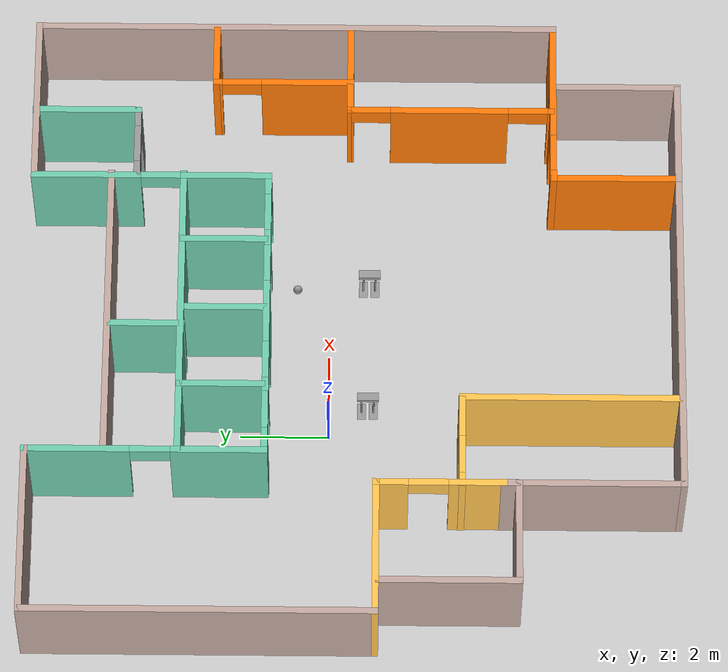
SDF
<sdf version="1.7">
 <world name="default">
  <light name="sun" type="directional">
   <pose>0 0 10 0 -0 0</pose>
   <diffuse>0.8 0.8 0.8 1</diffuse>
   <specular>0.2 0.2 0.2 1</specular>
   <attenuation>
    <range>1000</range>
    <constant>0.9</constant>
    <linear>0.01</linear>
    <quadratic>0.001</quadratic>
   </attenuation>
   <direction>-0.5 0.1 -0.9</direction>
   <spot><inner_angle>0</inner_angle><outer_angle>0</outer_angle><falloff>0</falloff></spot>
  </light>
  <model name="ground_plane">
   <static>1</static>
   <link name="link">
    <collision name="collision">
     <geometry><plane><normal>0 0 1</normal><size>100 100</size></plane></geometry>
     <surface>
      <contact><collide_bitmask>65535</collide_bitmask></contact>
      <friction><ode><mu>100</mu><mu2>50</mu2></ode></friction>
     </surface>
    </collision>
    <visual name="visual">
     <cast_shadows>0</cast_shadows>
     <geometry><plane><normal>0 0 1</normal><size>100 100</size></plane></geometry>
     <material>
      <script><uri>file://media/materials/scripts/gazebo.material</uri><name>Gazebo/Grey</name></script>
     </material>
    </visual>
   </link>
  </model>
  <gravity>0 0 -9.8</gravity>
  <magnetic_field>6e-06 2.3e-05 -4.2e-05</magnetic_field>
  <atmosphere type="adiabatic"/>
  <physics type="ode">
   <max_step_size>0.001</max_step_size>
   <real_time_factor>1</real_time_factor>
   <real_time_update_rate>1000</real_time_update_rate>
  </physics>
  <scene><ambient>0.4 0.4 0.4 1</ambient><background>0.7 0.7 0.7 1</background><shadows>1</shadows></scene>
  <spherical_coordinates>
   <surface_model>EARTH_WGS84</surface_model>
   <latitude_deg>0</latitude_deg>
   <longitude_deg>0</longitude_deg>
   <elevation>0</elevation>
   <heading_deg>0</heading_deg>
  </spherical_coordinates>
  <model name="Building">
   <pose>2.005 -0.57388 0 0 -0 0</pose>
   <link name="Wall_0">
    <collision name="Wall_0_Collision">
     <geometry><box><size>8 0.15 2.5</size></box></geometry>
     <pose>0 0 1.25 0 -0 0</pose>
    </collision>
    <visual name="Wall_0_Visual">
     <pose>0 0 1.25 0 -0 0</pose>
     <geometry><box><size>8 0.15 2.5</size></box></geometry>
     <material>
      <script><uri>file://media/materials/scripts/gazebo.material</uri><name>Gazebo/Grey</name></script>
      <ambient>0.760784 0.662745 0.627451 1</ambient>
     </material>
     <meta><layer>0</layer></meta>
    </visual>
    <pose>-7.275 3.41888 0 0 -0 1.5708</pose>
   </link>
   <link name="Wall_1">
    <collision name="Wall_1_Collision">
     <geometry><box><size>4 0.15 2.5</size></box></geometry>
     <pose>0 0 1.25 0 -0 0</pose>
    </collision>
    <visual name="Wall_1_Visual">
     <pose>0 0 1.25 0 -0 0</pose>
     <geometry><box><size>4 0.15 2.5</size></box></geometry>
     <material>
      <script><uri>file://media/materials/scripts/gazebo.material</uri><name>Gazebo/Grey</name></script>
      <ambient>0.760784 0.662745 0.627451 1</ambient>
     </material>
     <meta><layer>0</layer></meta>
    </visual>
    <pose>-5.35 7.34388 0 0 -0 0</pose>
   </link>
   <link name="Wall_10">
    <pose>5.35 -4.50612 0 0 -0 3.14159</pose>
    <visual name="Wall_10_Visual_0">
     <pose>-0.586196 0 1.25 0 -0 0</pose>
     <geometry><box><size>2.82761 0.15 2.5</size></box></geometry>
     <material>
      <script><uri>file://media/materials/scripts/gazebo.material</uri><name>Gazebo/Grey</name></script>
      <ambient>0.996078 0.47451 0.0196078 1</ambient>
     </material>
     <meta><layer>0</layer></meta>
    </visual>
    <collision name="Wall_10_Collision_0">
     <geometry><box><size>2.82761 0.15 2.5</size></box></geometry>
     <pose>-0.586196 0 1.25 0 -0 0</pose>
    </collision>
    <visual name="Wall_10_Visual_1">
     <pose>1.8638 0 1.25 0 -0 0</pose>
     <geometry><box><size>0.272392 0.15 2.5</size></box></geometry>
     <material>
      <script><uri>file://media/materials/scripts/gazebo.material</uri><name>Gazebo/Grey</name></script>
      <ambient>0.996078 0.47451 0.0196078 1</ambient>
     </material>
     <meta><layer>0</layer></meta>
    </visual>
    <collision name="Wall_10_Collision_1">
     <geometry><box><size>0.272392 0.15 2.5</size></box></geometry>
     <pose>1.8638 0 1.25 0 -0 0</pose>
    </collision>
    <visual name="Wall_10_Visual_2">
     <pose>1.27761 0 2.25 0 -0 0</pose>
     <geometry><box><size>0.9 0.15 0.5</size></box></geometry>
     <material>
      <script><uri>file://media/materials/scripts/gazebo.material</uri><name>Gazebo/Grey</name></script>
      <ambient>0.996078 0.47451 0.0196078 1</ambient>
     </material>
     <meta><layer>0</layer></meta>
    </visual>
    <collision name="Wall_10_Collision_2">
     <geometry><box><size>0.9 0.15 0.5</size></box></geometry>
     <pose>1.27761 0 2.25 0 -0 0</pose>
    </collision>
   </link>
   <link name="Wall_11">
    <collision name="Wall_11_Collision">
     <geometry><box><size>3 0.15 2.5</size></box></geometry>
     <pose>0 0 1.25 0 -0 0</pose>
    </collision>
    <visual name="Wall_11_Visual">
     <pose>0 0 1.25 0 -0 0</pose>
     <geometry><box><size>3 0.15 2.5</size></box></geometry>
     <material>
      <script><uri>file://media/materials/scripts/gazebo.material</uri><name>Gazebo/Grey</name></script>
      <ambient>0.996078 0.47451 0.0196078 1</ambient>
     </material>
     <meta><layer>0</layer></meta>
    </visual>
    <pose>3.425 -5.93112 0 0 -0 -1.5708</pose>
   </link>
   <link name="Wall_12">
    <collision name="Wall_12_Collision">
     <geometry><box><size>2.5 0.15 2.5</size></box></geometry>
     <pose>0 0 1.25 0 -0 0</pose>
    </collision>
    <visual name="Wall_12_Visual">
     <pose>0 0 1.25 0 -0 0</pose>
     <geometry><box><size>2.5 0.15 2.5</size></box></geometry>
     <material>
      <script><uri>file://media/materials/scripts/gazebo.material</uri><name>Gazebo/Grey</name></script>
      <ambient>0.760784 0.662745 0.627451 1</ambient>
     </material>
     <meta><layer>0</layer></meta>
    </visual>
    <pose>4.6 -7.35612 0 0 -0 0</pose>
   </link>
   <link name="Wall_13">
    <collision name="Wall_13_Collision">
     <geometry><box><size>3 0.15 2.5</size></box></geometry>
     <pose>0 0 1.25 0 -0 0</pose>
    </collision>
    <visual name="Wall_13_Visual">
     <pose>0 0 1.25 0 -0 0</pose>
     <geometry><box><size>3 0.15 2.5</size></box></geometry>
     <material>
      <script><uri>file://media/materials/scripts/gazebo.material</uri><name>Gazebo/Grey</name></script>
      <ambient>0.760784 0.662745 0.627451 1</ambient>
     </material>
     <meta><layer>0</layer></meta>
    </visual>
    <pose>5.775 -5.93112 0 0 -0 1.5708</pose>
   </link>
   <link name="Wall_15">
    <collision name="Wall_15_Collision">
     <geometry><box><size>3.25 0.15 2.5</size></box></geometry>
     <pose>0 0 1.25 0 -0 0</pose>
    </collision>
    <visual name="Wall_15_Visual">
     <pose>0 0 1.25 0 -0 0</pose>
     <geometry><box><size>3.25 0.15 2.5</size></box></geometry>
     <material>
      <script><uri>file://media/materials/scripts/gazebo.material</uri><name>Gazebo/Grey</name></script>
      <ambient>1 0.764706 0.305882 1</ambient>
     </material>
     <meta><layer>0</layer></meta>
    </visual>
    <pose>-5.725 -0.506122 0 0 -0 0</pose>
   </link>
   <link name="Wall_16">
    <pose>-4.175 -1.93112 0 0 -0 -1.5708</pose>
    <visual name="Wall_16_Visual_0">
     <pose>-1.10276 0 1.25 0 -0 0</pose>
     <geometry><box><size>0.794472 0.15 2.5</size></box></geometry>
     <material>
      <script><uri>file://media/materials/scripts/gazebo.material</uri><name>Gazebo/Grey</name></script>
      <ambient>1 0.764706 0.305882 1</ambient>
     </material>
     <meta><layer>0</layer></meta>
    </visual>
    <collision name="Wall_16_Collision_0">
     <geometry><box><size>0.794472 0.15 2.5</size></box></geometry>
     <pose>-1.10276 0 1.25 0 -0 0</pose>
    </collision>
    <visual name="Wall_16_Visual_1">
     <pose>0.847236 0 1.25 0 -0 0</pose>
     <geometry><box><size>1.30553 0.15 2.5</size></box></geometry>
     <material>
      <script><uri>file://media/materials/scripts/gazebo.material</uri><name>Gazebo/Grey</name></script>
      <ambient>1 0.764706 0.305882 1</ambient>
     </material>
     <meta><layer>0</layer></meta>
    </visual>
    <collision name="Wall_16_Collision_1">
     <geometry><box><size>1.30553 0.15 2.5</size></box></geometry>
     <pose>0.847236 0 1.25 0 -0 0</pose>
    </collision>
    <visual name="Wall_16_Visual_2">
     <pose>-0.255528 0 2.25 0 -0 0</pose>
     <geometry><box><size>0.9 0.15 0.5</size></box></geometry>
     <material>
      <script><uri>file://media/materials/scripts/gazebo.material</uri><name>Gazebo/Grey</name></script>
      <ambient>1 0.764706 0.305882 1</ambient>
     </material>
     <meta><layer>0</layer></meta>
    </visual>
    <collision name="Wall_16_Collision_2">
     <geometry><box><size>0.9 0.15 0.5</size></box></geometry>
     <pose>-0.255528 0 2.25 0 -0 0</pose>
    </collision>
   </link>
   <link name="Wall_2">
    <pose>-3.425 4.66888 0 0 -0 -1.5708</pose>
    <visual name="Wall_2_Visual_0">
     <pose>-1.53531 0 1.25 0 -0 0</pose>
     <geometry><box><size>2.42938 0.15 2.5</size></box></geometry>
     <material>
      <script><uri>file://media/materials/scripts/gazebo.material</uri><name>Gazebo/Grey</name></script>
      <ambient>0.435294 0.796078 0.67451 1</ambient>
     </material>
     <meta><layer>0</layer></meta>
    </visual>
    <collision name="Wall_2_Collision_0">
     <geometry><box><size>2.42938 0.15 2.5</size></box></geometry>
     <pose>-1.53531 0 1.25 0 -0 0</pose>
    </collision>
    <visual name="Wall_2_Visual_1">
     <pose>1.66469 0 1.25 0 -0 0</pose>
     <geometry><box><size>2.17062 0.15 2.5</size></box></geometry>
     <material>
      <script><uri>file://media/materials/scripts/gazebo.material</uri><name>Gazebo/Grey</name></script>
      <ambient>0.435294 0.796078 0.67451 1</ambient>
     </material>
     <meta><layer>0</layer></meta>
    </visual>
    <collision name="Wall_2_Collision_1">
     <geometry><box><size>2.17062 0.15 2.5</size></box></geometry>
     <pose>1.66469 0 1.25 0 -0 0</pose>
    </collision>
    <visual name="Wall_2_Visual_2">
     <pose>0.129378 0 2.25 0 -0 0</pose>
     <geometry><box><size>0.9 0.15 0.5</size></box></geometry>
     <material>
      <script><uri>file://media/materials/scripts/gazebo.material</uri><name>Gazebo/Grey</name></script>
      <ambient>0.435294 0.796078 0.67451 1</ambient>
     </material>
     <meta><layer>0</layer></meta>
    </visual>
    <collision name="Wall_2_Collision_2">
     <geometry><box><size>0.9 0.15 0.5</size></box></geometry>
     <pose>0.129378 0 2.25 0 -0 0</pose>
    </collision>
   </link>
   <link name="Wall_20">
    <collision name="Wall_20_Collision">
     <geometry><box><size>7.75 0.15 2.5</size></box></geometry>
     <pose>0 0 1.25 0 -0 0</pose>
    </collision>
    <visual name="Wall_20_Visual">
     <pose>0 0 1.25 0 -0 0</pose>
     <geometry><box><size>7.75 0.15 2.5</size></box></geometry>
     <material>
      <script><uri>file://media/materials/scripts/gazebo.material</uri><name>Gazebo/Grey</name></script>
      <ambient>0.760784 0.662745 0.627451 1</ambient>
     </material>
     <meta><layer>0</layer></meta>
    </visual>
    <pose>-0.375 -7.35612 0 0 -0 3.14159</pose>
   </link>
   <link name="Wall_21">
    <collision name="Wall_21_Collision">
     <geometry><box><size>4.15 0.15 2.5</size></box></geometry>
     <pose>0 0 1.25 0 -0 0</pose>
    </collision>
    <visual name="Wall_21_Visual">
     <pose>0 0 1.25 0 -0 0</pose>
     <geometry><box><size>4.15 0.15 2.5</size></box></geometry>
     <material>
      <script><uri>file://media/materials/scripts/gazebo.material</uri><name>Gazebo/Grey</name></script>
      <ambient>0.760784 0.662745 0.627451 1</ambient>
     </material>
     <meta><layer>0</layer></meta>
    </visual>
    <pose>-4.175 -5.35612 0 0 -0 1.5708</pose>
   </link>
   <link name="Wall_23">
    <collision name="Wall_23_Collision">
     <geometry><box><size>3.25 0.15 2.5</size></box></geometry>
     <pose>0 0 1.25 0 -0 0</pose>
    </collision>
    <visual name="Wall_23_Visual">
     <pose>0 0 1.25 0 -0 0</pose>
     <geometry><box><size>3.25 0.15 2.5</size></box></geometry>
     <material>
      <script><uri>file://media/materials/scripts/gazebo.material</uri><name>Gazebo/Grey</name></script>
      <ambient>0.760784 0.662745 0.627451 1</ambient>
     </material>
     <meta><layer>0</layer></meta>
    </visual>
    <pose>-6.52628 -2.1407 0 0 -0 -1.5708</pose>
   </link>
   <link name="Wall_24">
    <collision name="Wall_24_Collision">
     <geometry><box><size>2.5 0.15 2.5</size></box></geometry>
     <pose>0 0 1.25 0 -0 0</pose>
    </collision>
    <visual name="Wall_24_Visual">
     <pose>0 0 1.25 0 -0 0</pose>
     <geometry><box><size>2.5 0.15 2.5</size></box></geometry>
     <material>
      <script><uri>file://media/materials/scripts/gazebo.material</uri><name>Gazebo/Grey</name></script>
      <ambient>0.760784 0.662745 0.627451 1</ambient>
     </material>
     <meta><layer>0</layer></meta>
    </visual>
    <pose>-5.35128 -3.6907 0 0 -0 0</pose>
   </link>
   <link name="Wall_26">
    <pose>-3.13547 -2.42611 0 0 -0 0</pose>
    <visual name="Wall_26_Visual_0">
     <pose>-0.964923 0 1.25 0 -0 0</pose>
     <geometry><box><size>0.320154 0.15 2.5</size></box></geometry>
     <material>
      <script><uri>file://media/materials/scripts/gazebo.material</uri><name>Gazebo/Grey</name></script>
      <ambient>1 0.764706 0.305882 1</ambient>
     </material>
     <meta><layer>0</layer></meta>
    </visual>
    <collision name="Wall_26_Collision_0">
     <geometry><box><size>0.320154 0.15 2.5</size></box></geometry>
     <pose>-0.964923 0 1.25 0 -0 0</pose>
    </collision>
    <visual name="Wall_26_Visual_1">
     <pose>0.610077 0 1.25 0 -0 0</pose>
     <geometry><box><size>1.02985 0.15 2.5</size></box></geometry>
     <material>
      <script><uri>file://media/materials/scripts/gazebo.material</uri><name>Gazebo/Grey</name></script>
      <ambient>1 0.764706 0.305882 1</ambient>
     </material>
     <meta><layer>0</layer></meta>
    </visual>
    <collision name="Wall_26_Collision_1">
     <geometry><box><size>1.02985 0.15 2.5</size></box></geometry>
     <pose>0.610077 0 1.25 0 -0 0</pose>
    </collision>
    <visual name="Wall_26_Visual_2">
     <pose>-0.354846 0 2.25 0 -0 0</pose>
     <geometry><box><size>0.9 0.15 0.5</size></box></geometry>
     <material>
      <script><uri>file://media/materials/scripts/gazebo.material</uri><name>Gazebo/Grey</name></script>
      <ambient>1 0.764706 0.305882 1</ambient>
     </material>
     <meta><layer>0</layer></meta>
    </visual>
    <collision name="Wall_26_Collision_2">
     <geometry><box><size>0.9 0.15 0.5</size></box></geometry>
     <pose>-0.354846 0 2.25 0 -0 0</pose>
    </collision>
   </link>
   <link name="Wall_27">
    <collision name="Wall_27_Collision">
     <geometry><box><size>5 0.15 2.5</size></box></geometry>
     <pose>0 0 1.25 0 -0 0</pose>
    </collision>
    <visual name="Wall_27_Visual">
     <pose>0 0 1.25 0 -0 0</pose>
     <geometry><box><size>5 0.15 2.5</size></box></geometry>
     <material>
      <script><uri>file://media/materials/scripts/gazebo.material</uri><name>Gazebo/Grey</name></script>
      <ambient>1 0.764706 0.305882 1</ambient>
     </material>
     <meta><layer>0</layer></meta>
    </visual>
    <pose>-2.08547 -4.85111 0 0 -0 -1.5708</pose>
   </link>
   <link name="Wall_29">
    <collision name="Wall_29_Collision">
     <geometry><box><size>7 0.15 2.5</size></box></geometry>
     <pose>0 0 1.25 0 -0 0</pose>
    </collision>
    <visual name="Wall_29_Visual">
     <pose>0 0 1.25 0 -0 0</pose>
     <geometry><box><size>7 0.15 2.5</size></box></geometry>
     <material>
      <script><uri>file://media/materials/scripts/gazebo.material</uri><name>Gazebo/Grey</name></script>
      <ambient>0.760784 0.662745 0.627451 1</ambient>
     </material>
     <meta><layer>0</layer></meta>
    </visual>
    <pose>0.03754 5.58055 0 0 -0 0</pose>
   </link>
   <link name="Wall_3">
    <pose>0 1.99388 0 0 -0 0</pose>
    <visual name="Wall_3_Visual_0">
     <pose>-3.18715 0 1.25 0 -0 0</pose>
     <geometry><box><size>0.625708 0.15 2.5</size></box></geometry>
     <material>
      <script><uri>file://media/materials/scripts/gazebo.material</uri><name>Gazebo/Grey</name></script>
      <ambient>0.435294 0.796078 0.67451 1</ambient>
     </material>
     <meta><layer>0</layer></meta>
    </visual>
    <collision name="Wall_3_Collision_0">
     <geometry><box><size>0.625708 0.15 2.5</size></box></geometry>
     <pose>-3.18715 0 1.25 0 -0 0</pose>
    </collision>
    <visual name="Wall_3_Visual_1">
     <pose>-1.81083 0 1.25 0 -0 0</pose>
     <geometry><box><size>0.326928 0.15 2.5</size></box></geometry>
     <material>
      <script><uri>file://media/materials/scripts/gazebo.material</uri><name>Gazebo/Grey</name></script>
      <ambient>0.435294 0.796078 0.67451 1</ambient>
     </material>
     <meta><layer>0</layer></meta>
    </visual>
    <collision name="Wall_3_Collision_1">
     <geometry><box><size>0.326928 0.15 2.5</size></box></geometry>
     <pose>-1.81083 0 1.25 0 -0 0</pose>
    </collision>
    <visual name="Wall_3_Visual_2">
     <pose>0.00945 0 1.25 0 -0 0</pose>
     <geometry><box><size>1.51363 0.15 2.5</size></box></geometry>
     <material>
      <script><uri>file://media/materials/scripts/gazebo.material</uri><name>Gazebo/Grey</name></script>
      <ambient>0.435294 0.796078 0.67451 1</ambient>
     </material>
     <meta><layer>0</layer></meta>
    </visual>
    <collision name="Wall_3_Collision_2">
     <geometry><box><size>1.51363 0.15 2.5</size></box></geometry>
     <pose>0.00945 0 1.25 0 -0 0</pose>
    </collision>
    <visual name="Wall_3_Visual_3">
     <pose>1.8599 0 1.25 0 -0 0</pose>
     <geometry><box><size>0.387269 0.15 2.5</size></box></geometry>
     <material>
      <script><uri>file://media/materials/scripts/gazebo.material</uri><name>Gazebo/Grey</name></script>
      <ambient>0.435294 0.796078 0.67451 1</ambient>
     </material>
     <meta><layer>0</layer></meta>
    </visual>
    <collision name="Wall_3_Collision_3">
     <geometry><box><size>0.387269 0.15 2.5</size></box></geometry>
     <pose>1.8599 0 1.25 0 -0 0</pose>
    </collision>
    <visual name="Wall_3_Visual_4">
     <pose>3.22677 0 1.25 0 -0 0</pose>
     <geometry><box><size>0.546467 0.15 2.5</size></box></geometry>
     <material>
      <script><uri>file://media/materials/scripts/gazebo.material</uri><name>Gazebo/Grey</name></script>
      <ambient>0.435294 0.796078 0.67451 1</ambient>
     </material>
     <meta><layer>0</layer></meta>
    </visual>
    <collision name="Wall_3_Collision_4">
     <geometry><box><size>0.546467 0.15 2.5</size></box></geometry>
     <pose>3.22677 0 1.25 0 -0 0</pose>
    </collision>
    <visual name="Wall_3_Visual_5">
     <pose>-2.42429 0 2.25 0 -0 0</pose>
     <geometry><box><size>0.9 0.15 0.5</size></box></geometry>
     <material>
      <script><uri>file://media/materials/scripts/gazebo.material</uri><name>Gazebo/Grey</name></script>
      <ambient>0.435294 0.796078 0.67451 1</ambient>
     </material>
     <meta><layer>0</layer></meta>
    </visual>
    <collision name="Wall_3_Collision_5">
     <geometry><box><size>0.9 0.15 0.5</size></box></geometry>
     <pose>-2.42429 0 2.25 0 -0 0</pose>
    </collision>
    <visual name="Wall_3_Visual_6">
     <pose>-1.19736 0 2.25 0 -0 0</pose>
     <geometry><box><size>0.9 0.15 0.5</size></box></geometry>
     <material>
      <script><uri>file://media/materials/scripts/gazebo.material</uri><name>Gazebo/Grey</name></script>
      <ambient>0.435294 0.796078 0.67451 1</ambient>
     </material>
     <meta><layer>0</layer></meta>
    </visual>
    <collision name="Wall_3_Collision_6">
     <geometry><box><size>0.9 0.15 0.5</size></box></geometry>
     <pose>-1.19736 0 2.25 0 -0 0</pose>
    </collision>
    <visual name="Wall_3_Visual_7">
     <pose>1.21626 0 2.25 0 -0 0</pose>
     <geometry><box><size>0.9 0.15 0.5</size></box></geometry>
     <material>
      <script><uri>file://media/materials/scripts/gazebo.material</uri><name>Gazebo/Grey</name></script>
      <ambient>0.435294 0.796078 0.67451 1</ambient>
     </material>
     <meta><layer>0</layer></meta>
    </visual>
    <collision name="Wall_3_Collision_7">
     <geometry><box><size>0.9 0.15 0.5</size></box></geometry>
     <pose>1.21626 0 2.25 0 -0 0</pose>
    </collision>
    <visual name="Wall_3_Visual_8">
     <pose>2.50353 0 2.25 0 -0 0</pose>
     <geometry><box><size>0.9 0.15 0.5</size></box></geometry>
     <material>
      <script><uri>file://media/materials/scripts/gazebo.material</uri><name>Gazebo/Grey</name></script>
      <ambient>0.435294 0.796078 0.67451 1</ambient>
     </material>
     <meta><layer>0</layer></meta>
    </visual>
    <collision name="Wall_3_Collision_8">
     <geometry><box><size>0.9 0.15 0.5</size></box></geometry>
     <pose>2.50353 0 2.25 0 -0 0</pose>
    </collision>
   </link>
   <link name="Wall_31">
    <collision name="Wall_31_Collision">
     <geometry><box><size>7 0.15 2.5</size></box></geometry>
     <pose>0 0 1.25 0 -0 0</pose>
    </collision>
    <visual name="Wall_31_Visual">
     <pose>0 0 1.25 0 -0 0</pose>
     <geometry><box><size>7 0.15 2.5</size></box></geometry>
     <material>
      <script><uri>file://media/materials/scripts/gazebo.material</uri><name>Gazebo/Grey</name></script>
      <ambient>0.435294 0.796078 0.67451 1</ambient>
     </material>
     <meta><layer>0</layer></meta>
    </visual>
    <pose>0.03754 3.93133 0 0 -0 0</pose>
   </link>
   <link name="Wall_37">
    <collision name="Wall_37_Collision">
     <geometry><box><size>1.75 0.15 2.5</size></box></geometry>
     <pose>0 0 1.25 0 -0 0</pose>
    </collision>
    <visual name="Wall_37_Visual">
     <pose>0 0 1.25 0 -0 0</pose>
     <geometry><box><size>1.75 0.15 2.5</size></box></geometry>
     <material>
      <script><uri>file://media/materials/scripts/gazebo.material</uri><name>Gazebo/Grey</name></script>
      <ambient>0.435294 0.796078 0.67451 1</ambient>
     </material>
     <meta><layer>0</layer></meta>
    </visual>
    <pose>-0.313255 4.70425 0 0 -0 1.5708</pose>
   </link>
   <link name="Wall_39">
    <collision name="Wall_39_Collision">
     <geometry><box><size>2 0.15 2.5</size></box></geometry>
     <pose>0 0 1.25 0 -0 0</pose>
    </collision>
    <visual name="Wall_39_Visual">
     <pose>0 0 1.25 0 -0 0</pose>
     <geometry><box><size>2 0.15 2.5</size></box></geometry>
     <material>
      <script><uri>file://media/materials/scripts/gazebo.material</uri><name>Gazebo/Grey</name></script>
      <ambient>0.435294 0.796078 0.67451 1</ambient>
     </material>
     <meta><layer>0</layer></meta>
    </visual>
    <pose>0.106507 2.94427 0 0 -0 -1.5708</pose>
   </link>
   <link name="Wall_41">
    <collision name="Wall_41_Collision">
     <geometry><box><size>2 0.15 2.5</size></box></geometry>
     <pose>0 0 1.25 0 -0 0</pose>
    </collision>
    <visual name="Wall_41_Visual">
     <pose>0 0 1.25 0 -0 0</pose>
     <geometry><box><size>2 0.15 2.5</size></box></geometry>
     <material>
      <script><uri>file://media/materials/scripts/gazebo.material</uri><name>Gazebo/Grey</name></script>
      <ambient>0.435294 0.796078 0.67451 1</ambient>
     </material>
     <meta><layer>0</layer></meta>
    </visual>
    <pose>-1.79991 2.99674 0 0 -0 -1.5708</pose>
   </link>
   <link name="Wall_43">
    <collision name="Wall_43_Collision">
     <geometry><box><size>2 0.15 2.5</size></box></geometry>
     <pose>0 0 1.25 0 -0 0</pose>
    </collision>
    <visual name="Wall_43_Visual">
     <pose>0 0 1.25 0 -0 0</pose>
     <geometry><box><size>2 0.15 2.5</size></box></geometry>
     <material>
      <script><uri>file://media/materials/scripts/gazebo.material</uri><name>Gazebo/Grey</name></script>
      <ambient>0.435294 0.796078 0.67451 1</ambient>
     </material>
     <meta><layer>0</layer></meta>
    </visual>
    <pose>1.82053 2.97925 0 0 -0 -1.5708</pose>
   </link>
   <link name="Wall_45">
    <pose>4.29958 5.00612 0 0 -0 0</pose>
    <visual name="Wall_45_Visual_0">
     <pose>-0.695639 0 1.25 0 -0 0</pose>
     <geometry><box><size>0.358721 0.15 2.5</size></box></geometry>
     <material>
      <script><uri>file://media/materials/scripts/gazebo.material</uri><name>Gazebo/Grey</name></script>
      <ambient>1 1 1 1</ambient>
     </material>
     <meta><layer>0</layer></meta>
    </visual>
    <collision name="Wall_45_Collision_0">
     <geometry><box><size>0.358721 0.15 2.5</size></box></geometry>
     <pose>-0.695639 0 1.25 0 -0 0</pose>
    </collision>
    <visual name="Wall_45_Visual_1">
     <pose>0.629361 0 1.25 0 -0 0</pose>
     <geometry><box><size>0.491279 0.15 2.5</size></box></geometry>
     <material>
      <script><uri>file://media/materials/scripts/gazebo.material</uri><name>Gazebo/Grey</name></script>
      <ambient>1 1 1 1</ambient>
     </material>
     <meta><layer>0</layer></meta>
    </visual>
    <collision name="Wall_45_Collision_1">
     <geometry><box><size>0.491279 0.15 2.5</size></box></geometry>
     <pose>0.629361 0 1.25 0 -0 0</pose>
    </collision>
    <visual name="Wall_45_Visual_2">
     <pose>-0.066279 0 2.25 0 -0 0</pose>
     <geometry><box><size>0.9 0.15 0.5</size></box></geometry>
     <material>
      <script><uri>file://media/materials/scripts/gazebo.material</uri><name>Gazebo/Grey</name></script>
      <ambient>1 1 1 1</ambient>
     </material>
     <meta><layer>0</layer></meta>
    </visual>
    <collision name="Wall_45_Collision_2">
     <geometry><box><size>0.9 0.15 0.5</size></box></geometry>
     <pose>-0.066279 0 2.25 0 -0 0</pose>
    </collision>
   </link>
   <link name="Wall_46">
    <collision name="Wall_46_Collision">
     <geometry><box><size>2.5 0.15 2.5</size></box></geometry>
     <pose>0 0 1.25 0 -0 0</pose>
    </collision>
    <visual name="Wall_46_Visual">
     <pose>0 0 1.25 0 -0 0</pose>
     <geometry><box><size>2.5 0.15 2.5</size></box></geometry>
     <material>
      <script><uri>file://media/materials/scripts/gazebo.material</uri><name>Gazebo/Grey</name></script>
      <ambient>0.435294 0.796078 0.67451 1</ambient>
     </material>
     <meta><layer>0</layer></meta>
    </visual>
    <pose>5.09958 6.18112 0 0 -0 1.5708</pose>
   </link>
   <link name="Wall_51">
    <pose>5.13841 -2.15277 0 0 -0 1.5708</pose>
    <visual name="Wall_51_Visual_0">
     <pose>-2.30027 0 1.25 0 -0 0</pose>
     <geometry><box><size>0.149453 0.15 2.5</size></box></geometry>
     <material>
      <script><uri>file://media/materials/scripts/gazebo.material</uri><name>Gazebo/Grey</name></script>
      <ambient>0.996078 0.47451 0.0196078 1</ambient>
     </material>
     <meta><layer>0</layer></meta>
    </visual>
    <collision name="Wall_51_Collision_0">
     <geometry><box><size>0.149453 0.15 2.5</size></box></geometry>
     <pose>-2.30027 0 1.25 0 -0 0</pose>
    </collision>
    <visual name="Wall_51_Visual_1">
     <pose>0.024617 0 1.25 0 -0 0</pose>
     <geometry><box><size>2.70033 0.15 2.5</size></box></geometry>
     <material>
      <script><uri>file://media/materials/scripts/gazebo.material</uri><name>Gazebo/Grey</name></script>
      <ambient>0.996078 0.47451 0.0196078 1</ambient>
     </material>
     <meta><layer>0</layer></meta>
    </visual>
    <collision name="Wall_51_Collision_1">
     <geometry><box><size>2.70033 0.15 2.5</size></box></geometry>
     <pose>0.024617 0 1.25 0 -0 0</pose>
    </collision>
    <visual name="Wall_51_Visual_2">
     <pose>2.32489 0 1.25 0 -0 0</pose>
     <geometry><box><size>0.100218 0.15 2.5</size></box></geometry>
     <material>
      <script><uri>file://media/materials/scripts/gazebo.material</uri><name>Gazebo/Grey</name></script>
      <ambient>0.996078 0.47451 0.0196078 1</ambient>
     </material>
     <meta><layer>0</layer></meta>
    </visual>
    <collision name="Wall_51_Collision_2">
     <geometry><box><size>0.100218 0.15 2.5</size></box></geometry>
     <pose>2.32489 0 1.25 0 -0 0</pose>
    </collision>
    <visual name="Wall_51_Visual_3">
     <pose>-1.77555 0 2.25 0 -0 0</pose>
     <geometry><box><size>0.9 0.15 0.5</size></box></geometry>
     <material>
      <script><uri>file://media/materials/scripts/gazebo.material</uri><name>Gazebo/Grey</name></script>
      <ambient>0.996078 0.47451 0.0196078 1</ambient>
     </material>
     <meta><layer>0</layer></meta>
    </visual>
    <collision name="Wall_51_Collision_3">
     <geometry><box><size>0.9 0.15 0.5</size></box></geometry>
     <pose>-1.77555 0 2.25 0 -0 0</pose>
    </collision>
    <visual name="Wall_51_Visual_4">
     <pose>1.82478 0 2.25 0 -0 0</pose>
     <geometry><box><size>0.9 0.15 0.5</size></box></geometry>
     <material>
      <script><uri>file://media/materials/scripts/gazebo.material</uri><name>Gazebo/Grey</name></script>
      <ambient>0.996078 0.47451 0.0196078 1</ambient>
     </material>
     <meta><layer>0</layer></meta>
    </visual>
    <collision name="Wall_51_Collision_4">
     <geometry><box><size>0.9 0.15 0.5</size></box></geometry>
     <pose>1.82478 0 2.25 0 -0 0</pose>
    </collision>
   </link>
   <link name="Wall_52">
    <collision name="Wall_52_Collision">
     <geometry><box><size>2.25 0.15 2.5</size></box></geometry>
     <pose>0 0 1.25 0 -0 0</pose>
    </collision>
    <visual name="Wall_52_Visual">
     <pose>0 0 1.25 0 -0 0</pose>
     <geometry><box><size>2.25 0.15 2.5</size></box></geometry>
     <material>
      <script><uri>file://media/materials/scripts/gazebo.material</uri><name>Gazebo/Grey</name></script>
      <ambient>0.996078 0.47451 0.0196078 1</ambient>
     </material>
     <meta><layer>0</layer></meta>
    </visual>
    <pose>6.18841 0.147233 0 0 -0 0</pose>
   </link>
   <link name="Wall_54">
    <pose>5.84239 1.68463 0 0 -0 1.5708</pose>
    <visual name="Wall_54_Visual_0">
     <pose>-0.555402 0 1.25 0 -0 0</pose>
     <geometry><box><size>2.1392 0.15 2.5</size></box></geometry>
     <material>
      <script><uri>file://media/materials/scripts/gazebo.material</uri><name>Gazebo/Grey</name></script>
      <ambient>0.996078 0.47451 0.0196078 1</ambient>
     </material>
     <meta><layer>0</layer></meta>
    </visual>
    <collision name="Wall_54_Collision_0">
     <geometry><box><size>2.1392 0.15 2.5</size></box></geometry>
     <pose>-0.555402 0 1.25 0 -0 0</pose>
    </collision>
    <visual name="Wall_54_Visual_1">
     <pose>1.5196 0 1.25 0 -0 0</pose>
     <geometry><box><size>0.210803 0.15 2.5</size></box></geometry>
     <material>
      <script><uri>file://media/materials/scripts/gazebo.material</uri><name>Gazebo/Grey</name></script>
      <ambient>0.996078 0.47451 0.0196078 1</ambient>
     </material>
     <meta><layer>0</layer></meta>
    </visual>
    <collision name="Wall_54_Collision_1">
     <geometry><box><size>0.210803 0.15 2.5</size></box></geometry>
     <pose>1.5196 0 1.25 0 -0 0</pose>
    </collision>
    <visual name="Wall_54_Visual_2">
     <pose>0.964197 0 2.25 0 -0 0</pose>
     <geometry><box><size>0.9 0.15 0.5</size></box></geometry>
     <material>
      <script><uri>file://media/materials/scripts/gazebo.material</uri><name>Gazebo/Grey</name></script>
      <ambient>0.996078 0.47451 0.0196078 1</ambient>
     </material>
     <meta><layer>0</layer></meta>
    </visual>
    <collision name="Wall_54_Collision_2">
     <geometry><box><size>0.9 0.15 0.5</size></box></geometry>
     <pose>0.964197 0 2.25 0 -0 0</pose>
    </collision>
   </link>
   <link name="Wall_55">
    <collision name="Wall_55_Collision">
     <geometry><box><size>1.5 0.15 2.5</size></box></geometry>
     <pose>0 0 1.25 0 -0 0</pose>
    </collision>
    <visual name="Wall_55_Visual">
     <pose>0 0 1.25 0 -0 0</pose>
     <geometry><box><size>1.5 0.15 2.5</size></box></geometry>
     <material>
      <script><uri>file://media/materials/scripts/gazebo.material</uri><name>Gazebo/Grey</name></script>
      <ambient>0.996078 0.47451 0.0196078 1</ambient>
     </material>
     <meta><layer>0</layer></meta>
    </visual>
    <pose>6.51738 3.23463 0 0 -0 0</pose>
   </link>
   <link name="Wall_6">
    <pose>3.425 4.66888 0 0 -0 1.5708</pose>
    <visual name="Wall_6_Visual_0">
     <pose>-1.70492 0 1.25 0 -0 0</pose>
     <geometry><box><size>2.09017 0.15 2.5</size></box></geometry>
     <material>
      <script><uri>file://media/materials/scripts/gazebo.material</uri><name>Gazebo/Grey</name></script>
      <ambient>0.435294 0.796078 0.67451 1</ambient>
     </material>
     <meta><layer>0</layer></meta>
    </visual>
    <collision name="Wall_6_Collision_0">
     <geometry><box><size>2.09017 0.15 2.5</size></box></geometry>
     <pose>-1.70492 0 1.25 0 -0 0</pose>
    </collision>
    <visual name="Wall_6_Visual_1">
     <pose>1.49508 0 1.25 0 -0 0</pose>
     <geometry><box><size>2.50983 0.15 2.5</size></box></geometry>
     <material>
      <script><uri>file://media/materials/scripts/gazebo.material</uri><name>Gazebo/Grey</name></script>
      <ambient>0.435294 0.796078 0.67451 1</ambient>
     </material>
     <meta><layer>0</layer></meta>
    </visual>
    <collision name="Wall_6_Collision_1">
     <geometry><box><size>2.50983 0.15 2.5</size></box></geometry>
     <pose>1.49508 0 1.25 0 -0 0</pose>
    </collision>
    <visual name="Wall_6_Visual_2">
     <pose>-0.209832 0 2.25 0 -0 0</pose>
     <geometry><box><size>0.9 0.15 0.5</size></box></geometry>
     <material>
      <script><uri>file://media/materials/scripts/gazebo.material</uri><name>Gazebo/Grey</name></script>
      <ambient>0.435294 0.796078 0.67451 1</ambient>
     </material>
     <meta><layer>0</layer></meta>
    </visual>
    <collision name="Wall_6_Collision_2">
     <geometry><box><size>0.9 0.15 0.5</size></box></geometry>
     <pose>-0.209832 0 2.25 0 -0 0</pose>
    </collision>
   </link>
   <link name="Wall_8">
    <collision name="Wall_8_Collision">
     <geometry><box><size>4 0.15 2.5</size></box></geometry>
     <pose>0 0 1.25 0 -0 0</pose>
    </collision>
    <visual name="Wall_8_Visual">
     <pose>0 0 1.25 0 -0 0</pose>
     <geometry><box><size>4 0.15 2.5</size></box></geometry>
     <material>
      <script><uri>file://media/materials/scripts/gazebo.material</uri><name>Gazebo/Grey</name></script>
      <ambient>0.760784 0.662745 0.627451 1</ambient>
     </material>
     <meta><layer>0</layer></meta>
    </visual>
    <pose>5.35 7.34388 0 0 -0 0</pose>
   </link>
   <link name="Wall_9">
    <collision name="Wall_9_Collision">
     <geometry><box><size>12 0.15 2.5</size></box></geometry>
     <pose>0 0 1.25 0 -0 0</pose>
    </collision>
    <visual name="Wall_9_Visual">
     <pose>0 0 1.25 0 -0 0</pose>
     <geometry><box><size>12 0.15 2.5</size></box></geometry>
     <material>
      <script><uri>file://media/materials/scripts/gazebo.material</uri><name>Gazebo/Grey</name></script>
      <ambient>0.760784 0.662745 0.627451 1</ambient>
     </material>
     <meta><layer>0</layer></meta>
    </visual>
    <pose>7.275 1.41888 0 0 -0 -1.5708</pose>
   </link>
   <static>1</static>
  </model>
  <model name="HumanoidRobot">
   <link name="link_0">
    <inertial>
     <mass>1</mass>
     <inertia>
      <ixx>0.166667</ixx>
      <ixy>0</ixy>
      <ixz>0</ixz>
      <iyy>0.166667</iyy>
      <iyz>0</iyz>
      <izz>0.166667</izz>
     </inertia>
    </inertial>
    <pose>0.037224 0.016312 1 0 -0 0</pose>
    <visual name="visual">
     <geometry><box><size>0.2 0.5 0.1</size></box></geometry>
     <material>
      <lighting>1</lighting>
      <script><uri>file://media/materials/scripts/gazebo.material</uri><name>Gazebo/Grey</name></script>
      <shader type="pixel"><normal_map>__default__</normal_map></shader>
      <ambient>0.3 0.3 0.3 1</ambient>
      <diffuse>0.7 0.7 0.7 1</diffuse>
      <specular>0.01 0.01 0.01 1</specular>
      <emissive>0 0 0 1</emissive>
     </material>
    </visual>
    <collision name="collision">
     <geometry><box><size>0.2 0.5 0.1</size></box></geometry>
     <surface>
      <friction>
       <ode><mu>1</mu><mu2>1</mu2><fdir1>0 0 0</fdir1><slip1>0</slip1><slip2>0</slip2></ode>
       <torsional>
        <coefficient>1</coefficient>
        <patch_radius>0</patch_radius>
        <surface_radius>0</surface_radius>
        <use_patch_radius>1</use_patch_radius>
        <ode><slip>0</slip></ode>
       </torsional>
      </friction>
      <bounce><restitution_coefficient>0</restitution_coefficient><threshold>1e+06</threshold></bounce>
      <contact>
       <collide_without_contact>0</collide_without_contact>
       <collide_without_contact_bitmask>1</collide_without_contact_bitmask>
       <collide_bitmask>1</collide_bitmask>
       <ode>
        <soft_cfm>0</soft_cfm>
        <soft_erp>0.2</soft_erp>
        <kp>1e+13</kp>
        <kd>1</kd>
        <max_vel>0.01</max_vel>
        <min_depth>0</min_depth>
       </ode>
       <bullet>
        <split_impulse>1</split_impulse>
        <split_impulse_penetration_threshold>-0.01</split_impulse_penetration_threshold>
        <soft_cfm>0</soft_cfm>
        <soft_erp>0.2</soft_erp>
        <kp>1e+13</kp>
        <kd>1</kd>
       </bullet>
      </contact>
     </surface>
    </collision>
   </link>
   <link name="link_1">
    <inertial>
     <mass>1</mass>
     <inertia>
      <ixx>0.166667</ixx>
      <ixy>0</ixy>
      <ixz>0</ixz>
      <iyy>0.166667</iyy>
      <iyz>0</iyz>
      <izz>0.166667</izz>
     </inertia>
    </inertial>
    <pose>0.139866 -0.111553 0.00652 0 -0 0</pose>
    <visual name="visual">
     <geometry><box><size>0.4 0.2 0.009</size></box></geometry>
     <material>
      <lighting>1</lighting>
      <script><uri>file://media/materials/scripts/gazebo.material</uri><name>Gazebo/Grey</name></script>
      <shader type="pixel"><normal_map>__default__</normal_map></shader>
      <ambient>0.3 0.3 0.3 1</ambient>
      <diffuse>0.7 0.7 0.7 1</diffuse>
      <specular>0.01 0.01 0.01 1</specular>
      <emissive>0 0 0 1</emissive>
     </material>
    </visual>
    <collision name="collision">
     <geometry><box><size>0.4 0.2 0.009</size></box></geometry>
     <surface>
      <friction>
       <ode><mu>1</mu><mu2>1</mu2><fdir1>0 0 0</fdir1><slip1>0</slip1><slip2>0</slip2></ode>
       <torsional>
        <coefficient>1</coefficient>
        <patch_radius>0</patch_radius>
        <surface_radius>0</surface_radius>
        <use_patch_radius>1</use_patch_radius>
        <ode><slip>0</slip></ode>
       </torsional>
      </friction>
      <bounce><restitution_coefficient>0</restitution_coefficient><threshold>1e+06</threshold></bounce>
      <contact>
       <collide_without_contact>0</collide_without_contact>
       <collide_without_contact_bitmask>1</collide_without_contact_bitmask>
       <collide_bitmask>1</collide_bitmask>
       <ode>
        <soft_cfm>0</soft_cfm>
        <soft_erp>0.2</soft_erp>
        <kp>1e+13</kp>
        <kd>1</kd>
        <max_vel>0.01</max_vel>
        <min_depth>0</min_depth>
       </ode>
       <bullet>
        <split_impulse>1</split_impulse>
        <split_impulse_penetration_threshold>-0.01</split_impulse_penetration_threshold>
        <soft_cfm>0</soft_cfm>
        <soft_erp>0.2</soft_erp>
        <kp>1e+13</kp>
        <kd>1</kd>
       </bullet>
      </contact>
     </surface>
    </collision>
   </link>
   <link name="link_1_clone">
    <inertial>
     <mass>1</mass>
     <inertia>
      <ixx>0.166667</ixx>
      <ixy>0</ixy>
      <ixz>0</ixz>
      <iyy>0.166667</iyy>
      <iyz>0</iyz>
      <izz>0.166667</izz>
     </inertia>
    </inertial>
    <pose>0.137224 0.156083 0.00652 0 -0 0</pose>
    <visual name="visual">
     <geometry><box><size>0.4 0.2 0.009</size></box></geometry>
     <material>
      <lighting>1</lighting>
      <script><uri>file://media/materials/scripts/gazebo.material</uri><name>Gazebo/Grey</name></script>
      <shader type="pixel"><normal_map>__default__</normal_map></shader>
      <ambient>0.3 0.3 0.3 1</ambient>
      <diffuse>0.7 0.7 0.7 1</diffuse>
      <specular>0.01 0.01 0.01 1</specular>
      <emissive>0 0 0 1</emissive>
     </material>
    </visual>
    <collision name="collision">
     <geometry><box><size>0.4 0.2 0.009</size></box></geometry>
     <surface>
      <friction>
       <ode><mu>1</mu><mu2>1</mu2><fdir1>0 0 0</fdir1><slip1>0</slip1><slip2>0</slip2></ode>
       <torsional>
        <coefficient>1</coefficient>
        <patch_radius>0</patch_radius>
        <surface_radius>0</surface_radius>
        <use_patch_radius>1</use_patch_radius>
        <ode><slip>0</slip></ode>
       </torsional>
      </friction>
      <bounce><restitution_coefficient>0</restitution_coefficient><threshold>1e+06</threshold></bounce>
      <contact>
       <collide_without_contact>0</collide_without_contact>
       <collide_without_contact_bitmask>1</collide_without_contact_bitmask>
       <collide_bitmask>1</collide_bitmask>
       <ode>
        <soft_cfm>0</soft_cfm>
        <soft_erp>0.2</soft_erp>
        <kp>1e+13</kp>
        <kd>1</kd>
        <max_vel>0.01</max_vel>
        <min_depth>0</min_depth>
       </ode>
       <bullet>
        <split_impulse>1</split_impulse>
        <split_impulse_penetration_threshold>-0.01</split_impulse_penetration_threshold>
        <soft_cfm>0</soft_cfm>
        <soft_erp>0.2</soft_erp>
        <kp>1e+13</kp>
        <kd>1</kd>
       </bullet>
      </contact>
     </surface>
    </collision>
   </link>
   <link name="link_2">
    <inertial>
     <mass>1</mass>
     <inertia><ixx>0.145833</ixx><ixy>0</ixy><ixz>0</ixz><iyy>0.145833</iyy><iyz>0</iyz><izz>0.125</izz></inertia>
    </inertial>
    <pose>0.114643 -0.111553 0.22702 0 -0 0</pose>
    <visual name="visual">
     <geometry><cylinder><radius>0.02</radius><length>0.45</length></cylinder></geometry>
     <material>
      <lighting>1</lighting>
      <script><uri>file://media/materials/scripts/gazebo.material</uri><name>Gazebo/Grey</name></script>
      <shader type="pixel"><normal_map>__default__</normal_map></shader>
      <ambient>0.3 0.3 0.3 1</ambient>
      <diffuse>0.7 0.7 0.7 1</diffuse>
      <specular>0.01 0.01 0.01 1</specular>
      <emissive>0 0 0 1</emissive>
     </material>
    </visual>
    <collision name="collision">
     <geometry><cylinder><radius>0.02</radius><length>0.45</length></cylinder></geometry>
     <surface>
      <friction>
       <ode><mu>1</mu><mu2>1</mu2><fdir1>0 0 0</fdir1><slip1>0</slip1><slip2>0</slip2></ode>
       <torsional>
        <coefficient>1</coefficient>
        <patch_radius>0</patch_radius>
        <surface_radius>0</surface_radius>
        <use_patch_radius>1</use_patch_radius>
        <ode><slip>0</slip></ode>
       </torsional>
      </friction>
      <bounce><restitution_coefficient>0</restitution_coefficient><threshold>1e+06</threshold></bounce>
      <contact>
       <collide_without_contact>0</collide_without_contact>
       <collide_without_contact_bitmask>1</collide_without_contact_bitmask>
       <collide_bitmask>1</collide_bitmask>
       <ode>
        <soft_cfm>0</soft_cfm>
        <soft_erp>0.2</soft_erp>
        <kp>1e+13</kp>
        <kd>1</kd>
        <max_vel>0.01</max_vel>
        <min_depth>0</min_depth>
       </ode>
       <bullet>
        <split_impulse>1</split_impulse>
        <split_impulse_penetration_threshold>-0.01</split_impulse_penetration_threshold>
        <soft_cfm>0</soft_cfm>
        <soft_erp>0.2</soft_erp>
        <kp>1e+13</kp>
        <kd>1</kd>
       </bullet>
      </contact>
     </surface>
    </collision>
   </link>
   <link name="link_2_clone">
    <inertial>
     <mass>1</mass>
     <inertia><ixx>0.145833</ixx><ixy>0</ixy><ixz>0</ixz><iyy>0.145833</iyy><iyz>0</iyz><izz>0.125</izz></inertia>
    </inertial>
    <pose>0.064643 -0.113688 0.70101 0 -0 0</pose>
    <visual name="visual">
     <pose>0 0 0 0 -0.2 0</pose>
     <geometry><cylinder><radius>0.02</radius><length>0.5</length></cylinder></geometry>
     <material>
      <lighting>1</lighting>
      <script><uri>file://media/materials/scripts/gazebo.material</uri><name>Gazebo/Grey</name></script>
      <shader type="pixel"><normal_map>__default__</normal_map></shader>
      <ambient>0.3 0.3 0.3 1</ambient>
      <diffuse>0.7 0.7 0.7 1</diffuse>
      <specular>0.01 0.01 0.01 1</specular>
      <emissive>0 0 0 1</emissive>
     </material>
    </visual>
    <collision name="collision">
     <pose>0 0 0 0 -0.2 0</pose>
     <geometry><cylinder><radius>0.02</radius><length>0.5</length></cylinder></geometry>
     <surface>
      <friction>
       <ode><mu>1</mu><mu2>1</mu2><fdir1>0 0 0</fdir1><slip1>0</slip1><slip2>0</slip2></ode>
       <torsional>
        <coefficient>1</coefficient>
        <patch_radius>0</patch_radius>
        <surface_radius>0</surface_radius>
        <use_patch_radius>1</use_patch_radius>
        <ode><slip>0</slip></ode>
       </torsional>
      </friction>
      <bounce><restitution_coefficient>0</restitution_coefficient><threshold>1e+06</threshold></bounce>
      <contact>
       <collide_without_contact>0</collide_without_contact>
       <collide_without_contact_bitmask>1</collide_without_contact_bitmask>
       <collide_bitmask>1</collide_bitmask>
       <ode>
        <soft_cfm>0</soft_cfm>
        <soft_erp>0.2</soft_erp>
        <kp>1e+13</kp>
        <kd>1</kd>
        <max_vel>0.01</max_vel>
        <min_depth>0</min_depth>
       </ode>
       <bullet>
        <split_impulse>1</split_impulse>
        <split_impulse_penetration_threshold>-0.01</split_impulse_penetration_threshold>
        <soft_cfm>0</soft_cfm>
        <soft_erp>0.2</soft_erp>
        <kp>1e+13</kp>
        <kd>1</kd>
       </bullet>
      </contact>
     </surface>
    </collision>
   </link>
   <link name="link_2_clone_0">
    <inertial>
     <mass>1</mass>
     <inertia><ixx>0.145833</ixx><ixy>0</ixy><ixz>0</ixz><iyy>0.145833</iyy><iyz>0</iyz><izz>0.125</izz></inertia>
    </inertial>
    <pose>0.117224 0.156472 0.22702 0 -0 0</pose>
    <visual name="visual">
     <geometry><cylinder><radius>0.02</radius><length>0.45</length></cylinder></geometry>
     <material>
      <lighting>1</lighting>
      <script><uri>file://media/materials/scripts/gazebo.material</uri><name>Gazebo/Grey</name></script>
      <shader type="pixel"><normal_map>__default__</normal_map></shader>
      <ambient>0.3 0.3 0.3 1</ambient>
      <diffuse>0.7 0.7 0.7 1</diffuse>
      <specular>0.01 0.01 0.01 1</specular>
      <emissive>0 0 0 1</emissive>
     </material>
    </visual>
    <collision name="collision">
     <geometry><cylinder><radius>0.02</radius><length>0.45</length></cylinder></geometry>
     <surface>
      <friction>
       <ode><mu>1</mu><mu2>1</mu2><fdir1>0 0 0</fdir1><slip1>0</slip1><slip2>0</slip2></ode>
       <torsional>
        <coefficient>1</coefficient>
        <patch_radius>0</patch_radius>
        <surface_radius>0</surface_radius>
        <use_patch_radius>1</use_patch_radius>
        <ode><slip>0</slip></ode>
       </torsional>
      </friction>
      <bounce><restitution_coefficient>0</restitution_coefficient><threshold>1e+06</threshold></bounce>
      <contact>
       <collide_without_contact>0</collide_without_contact>
       <collide_without_contact_bitmask>1</collide_without_contact_bitmask>
       <collide_bitmask>1</collide_bitmask>
       <ode>
        <soft_cfm>0</soft_cfm>
        <soft_erp>0.2</soft_erp>
        <kp>1e+13</kp>
        <kd>1</kd>
        <max_vel>0.01</max_vel>
        <min_depth>0</min_depth>
       </ode>
       <bullet>
        <split_impulse>1</split_impulse>
        <split_impulse_penetration_threshold>-0.01</split_impulse_penetration_threshold>
        <soft_cfm>0</soft_cfm>
        <soft_erp>0.2</soft_erp>
        <kp>1e+13</kp>
        <kd>1</kd>
       </bullet>
      </contact>
     </surface>
    </collision>
   </link>
   <link name="link_2_clone_clone">
    <inertial>
     <mass>1</mass>
     <inertia><ixx>0.145833</ixx><ixy>0</ixy><ixz>0</ixz><iyy>0.145833</iyy><iyz>0</iyz><izz>0.125</izz></inertia>
    </inertial>
    <pose>0.067955 0.155472 0.70101 0 -0 0</pose>
    <visual name="visual">
     <pose>0 0 0 0 -0.2 0</pose>
     <geometry><cylinder><radius>0.02</radius><length>0.5</length></cylinder></geometry>
     <material>
      <lighting>1</lighting>
      <script><uri>file://media/materials/scripts/gazebo.material</uri><name>Gazebo/Grey</name></script>
      <shader type="pixel"><normal_map>__default__</normal_map></shader>
      <ambient>0.3 0.3 0.3 1</ambient>
      <diffuse>0.7 0.7 0.7 1</diffuse>
      <specular>0.01 0.01 0.01 1</specular>
      <emissive>0 0 0 1</emissive>
     </material>
    </visual>
    <collision name="collision">
     <pose>0 0 0 0 -0.2 0</pose>
     <geometry><cylinder><radius>0.02</radius><length>0.5</length></cylinder></geometry>
     <surface>
      <friction>
       <ode><mu>1</mu><mu2>1</mu2><fdir1>0 0 0</fdir1><slip1>0</slip1><slip2>0</slip2></ode>
       <torsional>
        <coefficient>1</coefficient>
        <patch_radius>0</patch_radius>
        <surface_radius>0</surface_radius>
        <use_patch_radius>1</use_patch_radius>
        <ode><slip>0</slip></ode>
       </torsional>
      </friction>
      <bounce><restitution_coefficient>0</restitution_coefficient><threshold>1e+06</threshold></bounce>
      <contact>
       <collide_without_contact>0</collide_without_contact>
       <collide_without_contact_bitmask>1</collide_without_contact_bitmask>
       <collide_bitmask>1</collide_bitmask>
       <ode>
        <soft_cfm>0</soft_cfm>
        <soft_erp>0.2</soft_erp>
        <kp>1e+13</kp>
        <kd>1</kd>
        <max_vel>0.01</max_vel>
        <min_depth>0</min_depth>
       </ode>
       <bullet>
        <split_impulse>1</split_impulse>
        <split_impulse_penetration_threshold>-0.01</split_impulse_penetration_threshold>
        <soft_cfm>0</soft_cfm>
        <soft_erp>0.2</soft_erp>
        <kp>1e+13</kp>
        <kd>1</kd>
       </bullet>
      </contact>
     </surface>
    </collision>
   </link>
   <joint name="link_0_JOINT_0" type="fixed">
    <parent>link_0</parent>
    <child>link_2_clone</child>
    <physics>
     <ode><limit><cfm>0</cfm><erp>0.2</erp></limit><suspension><cfm>0</cfm><erp>0.2</erp></suspension></ode>
    </physics>
   </joint>
   <joint name="link_0_JOINT_4" type="fixed">
    <parent>link_0</parent>
    <child>link_2_clone_clone</child>
    <physics>
     <ode><limit><cfm>0</cfm><erp>0.2</erp></limit><suspension><cfm>0</cfm><erp>0.2</erp></suspension></ode>
    </physics>
   </joint>
   <joint name="link_2_JOINT_3" type="fixed">
    <parent>link_2</parent>
    <child>link_1</child>
    <physics>
     <ode><limit><cfm>0</cfm><erp>0.2</erp></limit><suspension><cfm>0</cfm><erp>0.2</erp></suspension></ode>
    </physics>
   </joint>
   <joint name="link_2_clone_0_JOINT_6" type="fixed">
    <parent>link_2_clone_0</parent>
    <child>link_1_clone</child>
    <physics>
     <ode><limit><cfm>0</cfm><erp>0.2</erp></limit><suspension><cfm>0</cfm><erp>0.2</erp></suspension></ode>
    </physics>
   </joint>
   <joint name="link_2_clone_JOINT_2" type="fixed">
    <parent>link_2_clone</parent>
    <child>link_2</child>
    <pose>0 0 0.22 0 -0 0</pose>
    <physics>
     <ode><limit><cfm>0</cfm><erp>0.2</erp></limit><suspension><cfm>0</cfm><erp>0.2</erp></suspension></ode>
    </physics>
   </joint>
   <joint name="link_2_clone_clone_JOINT_5" type="fixed">
    <parent>link_2_clone_clone</parent>
    <child>link_2_clone_0</child>
    <pose>0 0 0.22 0 -0 0</pose>
    <physics>
     <ode><limit><cfm>0</cfm><erp>0.2</erp></limit><suspension><cfm>0</cfm><erp>0.2</erp></suspension></ode>
    </physics>
   </joint>
   <static>0</static>
   <pose>0.534995 -0.901858 -0.002021 -1e-06 2e-06 0.00347</pose>
  </model>
  <model name="HumanoidRobot_clone">
   <link name="link_0">
    <inertial>
     <mass>1</mass>
     <inertia>
      <ixx>0.166667</ixx>
      <ixy>0</ixy>
      <ixz>0</ixz>
      <iyy>0.166667</iyy>
      <iyz>0</iyz>
      <izz>0.166667</izz>
     </inertia>
    </inertial>
    <pose>0.037224 0.016312 1 0 -0 0</pose>
    <visual name="visual">
     <geometry><box><size>0.2 0.5 0.1</size></box></geometry>
     <material>
      <lighting>1</lighting>
      <script><uri>file://media/materials/scripts/gazebo.material</uri><name>Gazebo/Grey</name></script>
      <shader type="pixel"><normal_map>__default__</normal_map></shader>
      <ambient>0.3 0.3 0.3 1</ambient>
      <diffuse>0.7 0.7 0.7 1</diffuse>
      <specular>0.01 0.01 0.01 1</specular>
      <emissive>0 0 0 1</emissive>
     </material>
    </visual>
    <collision name="collision">
     <geometry><box><size>0.2 0.5 0.1</size></box></geometry>
     <surface>
      <friction>
       <ode><mu>1</mu><mu2>1</mu2><fdir1>0 0 0</fdir1><slip1>0</slip1><slip2>0</slip2></ode>
       <torsional>
        <coefficient>1</coefficient>
        <patch_radius>0</patch_radius>
        <surface_radius>0</surface_radius>
        <use_patch_radius>1</use_patch_radius>
        <ode><slip>0</slip></ode>
       </torsional>
      </friction>
      <bounce><restitution_coefficient>0</restitution_coefficient><threshold>1e+06</threshold></bounce>
      <contact>
       <collide_without_contact>0</collide_without_contact>
       <collide_without_contact_bitmask>1</collide_without_contact_bitmask>
       <collide_bitmask>1</collide_bitmask>
       <ode>
        <soft_cfm>0</soft_cfm>
        <soft_erp>0.2</soft_erp>
        <kp>1e+13</kp>
        <kd>1</kd>
        <max_vel>0.01</max_vel>
        <min_depth>0</min_depth>
       </ode>
       <bullet>
        <split_impulse>1</split_impulse>
        <split_impulse_penetration_threshold>-0.01</split_impulse_penetration_threshold>
        <soft_cfm>0</soft_cfm>
        <soft_erp>0.2</soft_erp>
        <kp>1e+13</kp>
        <kd>1</kd>
       </bullet>
      </contact>
     </surface>
    </collision>
   </link>
   <link name="link_1">
    <inertial>
     <mass>1</mass>
     <inertia>
      <ixx>0.166667</ixx>
      <ixy>0</ixy>
      <ixz>0</ixz>
      <iyy>0.166667</iyy>
      <iyz>0</iyz>
      <izz>0.166667</izz>
     </inertia>
    </inertial>
    <pose>0.139866 -0.111553 0.00652 0 -0 0</pose>
    <visual name="visual">
     <geometry><box><size>0.4 0.2 0.009</size></box></geometry>
     <material>
      <lighting>1</lighting>
      <script><uri>file://media/materials/scripts/gazebo.material</uri><name>Gazebo/Grey</name></script>
      <shader type="pixel"><normal_map>__default__</normal_map></shader>
      <ambient>0.3 0.3 0.3 1</ambient>
      <diffuse>0.7 0.7 0.7 1</diffuse>
      <specular>0.01 0.01 0.01 1</specular>
      <emissive>0 0 0 1</emissive>
     </material>
    </visual>
    <collision name="collision">
     <geometry><box><size>0.4 0.2 0.009</size></box></geometry>
     <surface>
      <friction>
       <ode><mu>1</mu><mu2>1</mu2><fdir1>0 0 0</fdir1><slip1>0</slip1><slip2>0</slip2></ode>
       <torsional>
        <coefficient>1</coefficient>
        <patch_radius>0</patch_radius>
        <surface_radius>0</surface_radius>
        <use_patch_radius>1</use_patch_radius>
        <ode><slip>0</slip></ode>
       </torsional>
      </friction>
      <bounce><restitution_coefficient>0</restitution_coefficient><threshold>1e+06</threshold></bounce>
      <contact>
       <collide_without_contact>0</collide_without_contact>
       <collide_without_contact_bitmask>1</collide_without_contact_bitmask>
       <collide_bitmask>1</collide_bitmask>
       <ode>
        <soft_cfm>0</soft_cfm>
        <soft_erp>0.2</soft_erp>
        <kp>1e+13</kp>
        <kd>1</kd>
        <max_vel>0.01</max_vel>
        <min_depth>0</min_depth>
       </ode>
       <bullet>
        <split_impulse>1</split_impulse>
        <split_impulse_penetration_threshold>-0.01</split_impulse_penetration_threshold>
        <soft_cfm>0</soft_cfm>
        <soft_erp>0.2</soft_erp>
        <kp>1e+13</kp>
        <kd>1</kd>
       </bullet>
      </contact>
     </surface>
    </collision>
   </link>
   <link name="link_1_clone">
    <inertial>
     <mass>1</mass>
     <inertia>
      <ixx>0.166667</ixx>
      <ixy>0</ixy>
      <ixz>0</ixz>
      <iyy>0.166667</iyy>
      <iyz>0</iyz>
      <izz>0.166667</izz>
     </inertia>
    </inertial>
    <pose>0.137224 0.156083 0.00652 0 -0 0</pose>
    <visual name="visual">
     <geometry><box><size>0.4 0.2 0.009</size></box></geometry>
     <material>
      <lighting>1</lighting>
      <script><uri>file://media/materials/scripts/gazebo.material</uri><name>Gazebo/Grey</name></script>
      <shader type="pixel"><normal_map>__default__</normal_map></shader>
      <ambient>0.3 0.3 0.3 1</ambient>
      <diffuse>0.7 0.7 0.7 1</diffuse>
      <specular>0.01 0.01 0.01 1</specular>
      <emissive>0 0 0 1</emissive>
     </material>
    </visual>
    <collision name="collision">
     <geometry><box><size>0.4 0.2 0.009</size></box></geometry>
     <surface>
      <friction>
       <ode><mu>1</mu><mu2>1</mu2><fdir1>0 0 0</fdir1><slip1>0</slip1><slip2>0</slip2></ode>
       <torsional>
        <coefficient>1</coefficient>
        <patch_radius>0</patch_radius>
        <surface_radius>0</surface_radius>
        <use_patch_radius>1</use_patch_radius>
        <ode><slip>0</slip></ode>
       </torsional>
      </friction>
      <bounce><restitution_coefficient>0</restitution_coefficient><threshold>1e+06</threshold></bounce>
      <contact>
       <collide_without_contact>0</collide_without_contact>
       <collide_without_contact_bitmask>1</collide_without_contact_bitmask>
       <collide_bitmask>1</collide_bitmask>
       <ode>
        <soft_cfm>0</soft_cfm>
        <soft_erp>0.2</soft_erp>
        <kp>1e+13</kp>
        <kd>1</kd>
        <max_vel>0.01</max_vel>
        <min_depth>0</min_depth>
       </ode>
       <bullet>
        <split_impulse>1</split_impulse>
        <split_impulse_penetration_threshold>-0.01</split_impulse_penetration_threshold>
        <soft_cfm>0</soft_cfm>
        <soft_erp>0.2</soft_erp>
        <kp>1e+13</kp>
        <kd>1</kd>
       </bullet>
      </contact>
     </surface>
    </collision>
   </link>
   <link name="link_2">
    <inertial>
     <mass>1</mass>
     <inertia><ixx>0.145833</ixx><ixy>0</ixy><ixz>0</ixz><iyy>0.145833</iyy><iyz>0</iyz><izz>0.125</izz></inertia>
    </inertial>
    <pose>0.114643 -0.111553 0.22702 0 -0 0</pose>
    <visual name="visual">
     <geometry><cylinder><radius>0.02</radius><length>0.45</length></cylinder></geometry>
     <material>
      <lighting>1</lighting>
      <script><uri>file://media/materials/scripts/gazebo.material</uri><name>Gazebo/Grey</name></script>
      <shader type="pixel"><normal_map>__default__</normal_map></shader>
      <ambient>0.3 0.3 0.3 1</ambient>
      <diffuse>0.7 0.7 0.7 1</diffuse>
      <specular>0.01 0.01 0.01 1</specular>
      <emissive>0 0 0 1</emissive>
     </material>
    </visual>
    <collision name="collision">
     <geometry><cylinder><radius>0.02</radius><length>0.45</length></cylinder></geometry>
     <surface>
      <friction>
       <ode><mu>1</mu><mu2>1</mu2><fdir1>0 0 0</fdir1><slip1>0</slip1><slip2>0</slip2></ode>
       <torsional>
        <coefficient>1</coefficient>
        <patch_radius>0</patch_radius>
        <surface_radius>0</surface_radius>
        <use_patch_radius>1</use_patch_radius>
        <ode><slip>0</slip></ode>
       </torsional>
      </friction>
      <bounce><restitution_coefficient>0</restitution_coefficient><threshold>1e+06</threshold></bounce>
      <contact>
       <collide_without_contact>0</collide_without_contact>
       <collide_without_contact_bitmask>1</collide_without_contact_bitmask>
       <collide_bitmask>1</collide_bitmask>
       <ode>
        <soft_cfm>0</soft_cfm>
        <soft_erp>0.2</soft_erp>
        <kp>1e+13</kp>
        <kd>1</kd>
        <max_vel>0.01</max_vel>
        <min_depth>0</min_depth>
       </ode>
       <bullet>
        <split_impulse>1</split_impulse>
        <split_impulse_penetration_threshold>-0.01</split_impulse_penetration_threshold>
        <soft_cfm>0</soft_cfm>
        <soft_erp>0.2</soft_erp>
        <kp>1e+13</kp>
        <kd>1</kd>
       </bullet>
      </contact>
     </surface>
    </collision>
   </link>
   <link name="link_2_clone">
    <inertial>
     <mass>1</mass>
     <inertia><ixx>0.145833</ixx><ixy>0</ixy><ixz>0</ixz><iyy>0.145833</iyy><iyz>0</iyz><izz>0.125</izz></inertia>
    </inertial>
    <pose>0.064643 -0.113688 0.70101 0 -0 0</pose>
    <visual name="visual">
     <pose>0 0 0 0 -0.2 0</pose>
     <geometry><cylinder><radius>0.02</radius><length>0.5</length></cylinder></geometry>
     <material>
      <lighting>1</lighting>
      <script><uri>file://media/materials/scripts/gazebo.material</uri><name>Gazebo/Grey</name></script>
      <shader type="pixel"><normal_map>__default__</normal_map></shader>
      <ambient>0.3 0.3 0.3 1</ambient>
      <diffuse>0.7 0.7 0.7 1</diffuse>
      <specular>0.01 0.01 0.01 1</specular>
      <emissive>0 0 0 1</emissive>
     </material>
    </visual>
    <collision name="collision">
     <pose>0 0 0 0 -0.2 0</pose>
     <geometry><cylinder><radius>0.02</radius><length>0.5</length></cylinder></geometry>
     <surface>
      <friction>
       <ode><mu>1</mu><mu2>1</mu2><fdir1>0 0 0</fdir1><slip1>0</slip1><slip2>0</slip2></ode>
       <torsional>
        <coefficient>1</coefficient>
        <patch_radius>0</patch_radius>
        <surface_radius>0</surface_radius>
        <use_patch_radius>1</use_patch_radius>
        <ode><slip>0</slip></ode>
       </torsional>
      </friction>
      <bounce><restitution_coefficient>0</restitution_coefficient><threshold>1e+06</threshold></bounce>
      <contact>
       <collide_without_contact>0</collide_without_contact>
       <collide_without_contact_bitmask>1</collide_without_contact_bitmask>
       <collide_bitmask>1</collide_bitmask>
       <ode>
        <soft_cfm>0</soft_cfm>
        <soft_erp>0.2</soft_erp>
        <kp>1e+13</kp>
        <kd>1</kd>
        <max_vel>0.01</max_vel>
        <min_depth>0</min_depth>
       </ode>
       <bullet>
        <split_impulse>1</split_impulse>
        <split_impulse_penetration_threshold>-0.01</split_impulse_penetration_threshold>
        <soft_cfm>0</soft_cfm>
        <soft_erp>0.2</soft_erp>
        <kp>1e+13</kp>
        <kd>1</kd>
       </bullet>
      </contact>
     </surface>
    </collision>
   </link>
   <link name="link_2_clone_0">
    <inertial>
     <mass>1</mass>
     <inertia><ixx>0.145833</ixx><ixy>0</ixy><ixz>0</ixz><iyy>0.145833</iyy><iyz>0</iyz><izz>0.125</izz></inertia>
    </inertial>
    <pose>0.117224 0.156472 0.22702 0 -0 0</pose>
    <visual name="visual">
     <geometry><cylinder><radius>0.02</radius><length>0.45</length></cylinder></geometry>
     <material>
      <lighting>1</lighting>
      <script><uri>file://media/materials/scripts/gazebo.material</uri><name>Gazebo/Grey</name></script>
      <shader type="pixel"><normal_map>__default__</normal_map></shader>
      <ambient>0.3 0.3 0.3 1</ambient>
      <diffuse>0.7 0.7 0.7 1</diffuse>
      <specular>0.01 0.01 0.01 1</specular>
      <emissive>0 0 0 1</emissive>
     </material>
    </visual>
    <collision name="collision">
     <geometry><cylinder><radius>0.02</radius><length>0.45</length></cylinder></geometry>
     <surface>
      <friction>
       <ode><mu>1</mu><mu2>1</mu2><fdir1>0 0 0</fdir1><slip1>0</slip1><slip2>0</slip2></ode>
       <torsional>
        <coefficient>1</coefficient>
        <patch_radius>0</patch_radius>
        <surface_radius>0</surface_radius>
        <use_patch_radius>1</use_patch_radius>
        <ode><slip>0</slip></ode>
       </torsional>
      </friction>
      <bounce><restitution_coefficient>0</restitution_coefficient><threshold>1e+06</threshold></bounce>
      <contact>
       <collide_without_contact>0</collide_without_contact>
       <collide_without_contact_bitmask>1</collide_without_contact_bitmask>
       <collide_bitmask>1</collide_bitmask>
       <ode>
        <soft_cfm>0</soft_cfm>
        <soft_erp>0.2</soft_erp>
        <kp>1e+13</kp>
        <kd>1</kd>
        <max_vel>0.01</max_vel>
        <min_depth>0</min_depth>
       </ode>
       <bullet>
        <split_impulse>1</split_impulse>
        <split_impulse_penetration_threshold>-0.01</split_impulse_penetration_threshold>
        <soft_cfm>0</soft_cfm>
        <soft_erp>0.2</soft_erp>
        <kp>1e+13</kp>
        <kd>1</kd>
       </bullet>
      </contact>
     </surface>
    </collision>
   </link>
   <link name="link_2_clone_clone">
    <inertial>
     <mass>1</mass>
     <inertia><ixx>0.145833</ixx><ixy>0</ixy><ixz>0</ixz><iyy>0.145833</iyy><iyz>0</iyz><izz>0.125</izz></inertia>
    </inertial>
    <pose>0.067955 0.155472 0.70101 0 -0 0</pose>
    <visual name="visual">
     <pose>0 0 0 0 -0.2 0</pose>
     <geometry><cylinder><radius>0.02</radius><length>0.5</length></cylinder></geometry>
     <material>
      <lighting>1</lighting>
      <script><uri>file://media/materials/scripts/gazebo.material</uri><name>Gazebo/Grey</name></script>
      <shader type="pixel"><normal_map>__default__</normal_map></shader>
      <ambient>0.3 0.3 0.3 1</ambient>
      <diffuse>0.7 0.7 0.7 1</diffuse>
      <specular>0.01 0.01 0.01 1</specular>
      <emissive>0 0 0 1</emissive>
     </material>
    </visual>
    <collision name="collision">
     <pose>0 0 0 0 -0.2 0</pose>
     <geometry><cylinder><radius>0.02</radius><length>0.5</length></cylinder></geometry>
     <surface>
      <friction>
       <ode><mu>1</mu><mu2>1</mu2><fdir1>0 0 0</fdir1><slip1>0</slip1><slip2>0</slip2></ode>
       <torsional>
        <coefficient>1</coefficient>
        <patch_radius>0</patch_radius>
        <surface_radius>0</surface_radius>
        <use_patch_radius>1</use_patch_radius>
        <ode><slip>0</slip></ode>
       </torsional>
      </friction>
      <bounce><restitution_coefficient>0</restitution_coefficient><threshold>1e+06</threshold></bounce>
      <contact>
       <collide_without_contact>0</collide_without_contact>
       <collide_without_contact_bitmask>1</collide_without_contact_bitmask>
       <collide_bitmask>1</collide_bitmask>
       <ode>
        <soft_cfm>0</soft_cfm>
        <soft_erp>0.2</soft_erp>
        <kp>1e+13</kp>
        <kd>1</kd>
        <max_vel>0.01</max_vel>
        <min_depth>0</min_depth>
       </ode>
       <bullet>
        <split_impulse>1</split_impulse>
        <split_impulse_penetration_threshold>-0.01</split_impulse_penetration_threshold>
        <soft_cfm>0</soft_cfm>
        <soft_erp>0.2</soft_erp>
        <kp>1e+13</kp>
        <kd>1</kd>
       </bullet>
      </contact>
     </surface>
    </collision>
   </link>
   <joint name="link_0_JOINT_0" type="fixed">
    <parent>link_0</parent>
    <child>link_2_clone</child>
    <physics>
     <ode><limit><cfm>0</cfm><erp>0.2</erp></limit><suspension><cfm>0</cfm><erp>0.2</erp></suspension></ode>
    </physics>
   </joint>
   <joint name="link_0_JOINT_4" type="fixed">
    <parent>link_0</parent>
    <child>link_2_clone_clone</child>
    <physics>
     <ode><limit><cfm>0</cfm><erp>0.2</erp></limit><suspension><cfm>0</cfm><erp>0.2</erp></suspension></ode>
    </physics>
   </joint>
   <joint name="link_2_JOINT_3" type="fixed">
    <parent>link_2</parent>
    <child>link_1</child>
    <physics>
     <ode><limit><cfm>0</cfm><erp>0.2</erp></limit><suspension><cfm>0</cfm><erp>0.2</erp></suspension></ode>
    </physics>
   </joint>
   <joint name="link_2_clone_0_JOINT_6" type="fixed">
    <parent>link_2_clone_0</parent>
    <child>link_1_clone</child>
    <physics>
     <ode><limit><cfm>0</cfm><erp>0.2</erp></limit><suspension><cfm>0</cfm><erp>0.2</erp></suspension></ode>
    </physics>
   </joint>
   <joint name="link_2_clone_JOINT_2" type="fixed">
    <parent>link_2_clone</parent>
    <child>link_2</child>
    <pose>0 0 0.22 0 -0 0</pose>
    <physics>
     <ode><limit><cfm>0</cfm><erp>0.2</erp></limit><suspension><cfm>0</cfm><erp>0.2</erp></suspension></ode>
    </physics>
   </joint>
   <joint name="link_2_clone_clone_JOINT_5" type="fixed">
    <parent>link_2_clone_clone</parent>
    <child>link_2_clone_0</child>
    <pose>0 0 0.22 0 -0 0</pose>
    <physics>
     <ode><limit><cfm>0</cfm><erp>0.2</erp></limit><suspension><cfm>0</cfm><erp>0.2</erp></suspension></ode>
    </physics>
   </joint>
   <static>0</static>
   <pose>3.62416 -0.91817 -0.00202 3e-06 -1e-06 0.006888</pose>
  </model>
  <model name="my_ball">
   <link name="link_0">
    <inertial>
     <mass>1</mass>
     <inertia><ixx>0.1</ixx><ixy>0</ixy><ixz>0</ixz><iyy>0.1</iyy><iyz>0</iyz><izz>0.1</izz></inertia>
    </inertial>
    <visual name="visual">
     <geometry><sphere><radius>0.1</radius></sphere></geometry>
     <material>
      <lighting>1</lighting>
      <script><uri>file://media/materials/scripts/gazebo.material</uri><name>Gazebo/Grey</name></script>
      <shader type="pixel"><normal_map>__default__</normal_map></shader>
      <ambient>1 1 1 1</ambient>
      <diffuse>1 1 1 1</diffuse>
      <specular>1 1 1 1</specular>
      <emissive>1 1 1 1</emissive>
     </material>
    </visual>
    <collision name="collision">
     <geometry><sphere><radius>0.1</radius></sphere></geometry>
     <surface>
      <friction>
       <ode><mu>1</mu><mu2>1</mu2><fdir1>0 0 0</fdir1><slip1>0</slip1><slip2>0</slip2></ode>
       <torsional>
        <coefficient>1</coefficient>
        <patch_radius>0</patch_radius>
        <surface_radius>0</surface_radius>
        <use_patch_radius>1</use_patch_radius>
        <ode><slip>0</slip></ode>
       </torsional>
      </friction>
      <bounce><restitution_coefficient>0</restitution_coefficient><threshold>1e+06</threshold></bounce>
      <contact>
       <collide_without_contact>0</collide_without_contact>
       <collide_without_contact_bitmask>1</collide_without_contact_bitmask>
       <collide_bitmask>1</collide_bitmask>
       <ode>
        <soft_cfm>0</soft_cfm>
        <soft_erp>0.2</soft_erp>
        <kp>1e+13</kp>
        <kd>1</kd>
        <max_vel>0.01</max_vel>
        <min_depth>0</min_depth>
       </ode>
       <bullet>
        <split_impulse>1</split_impulse>
        <split_impulse_penetration_threshold>-0.01</split_impulse_penetration_threshold>
        <soft_cfm>0</soft_cfm>
        <soft_erp>0.2</soft_erp>
        <kp>1e+13</kp>
        <kd>1</kd>
       </bullet>
      </contact>
     </surface>
    </collision>
   </link>
   <static>0</static>
   <pose>3.70434 0.75179 0.1 0 -0 0</pose>
  </model>
 </world>
</sdf>
